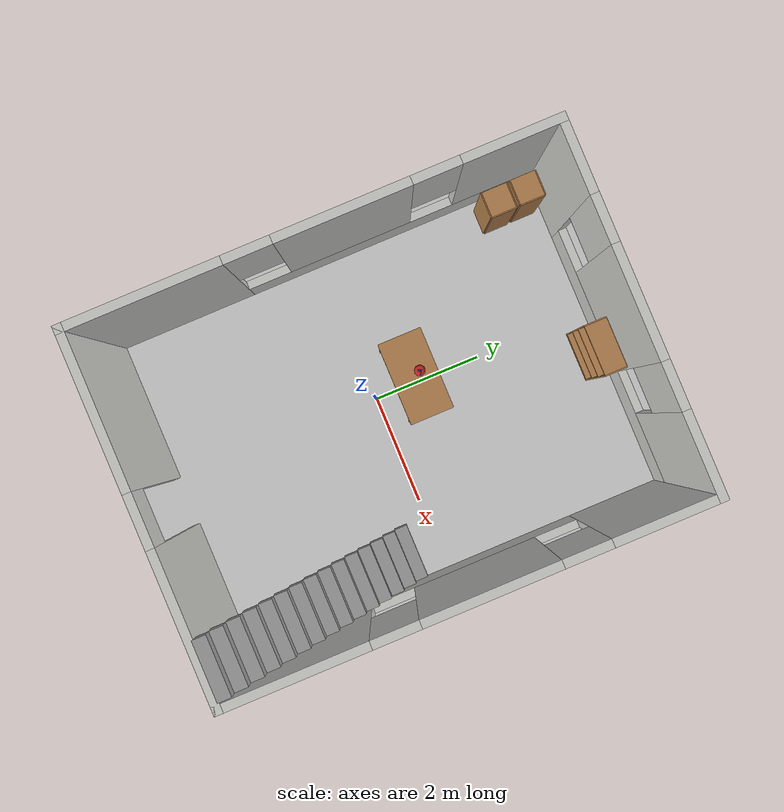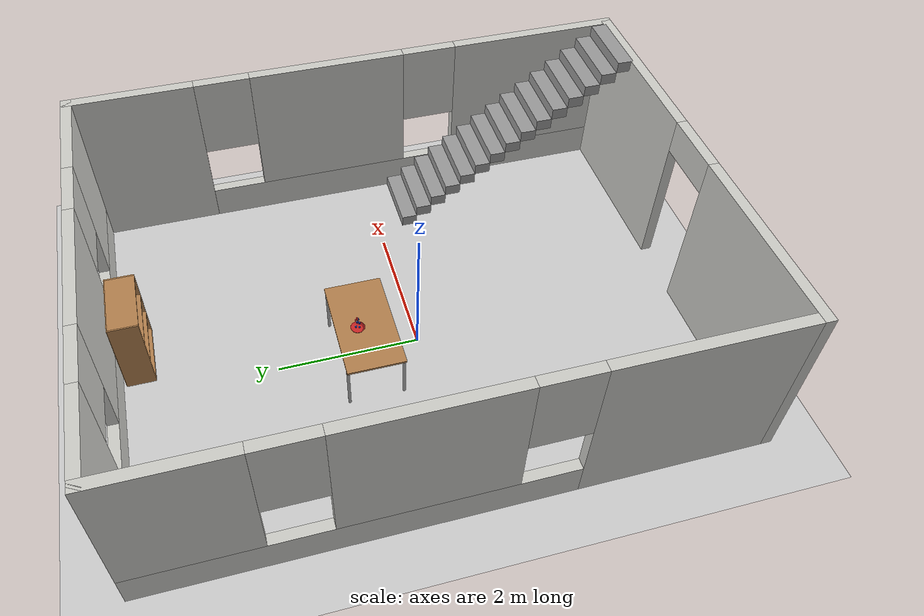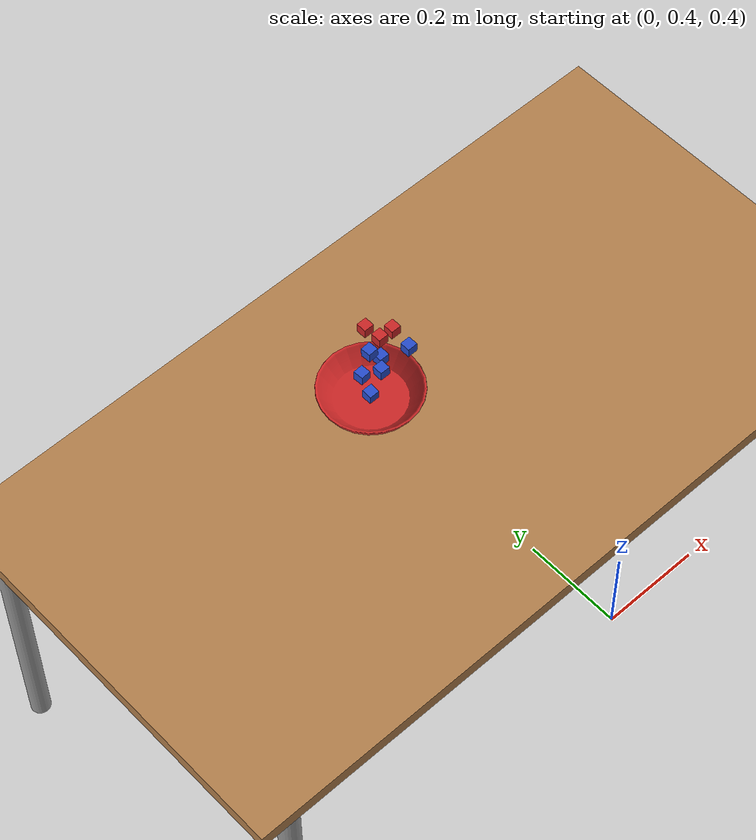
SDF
<sdf version="1.6">
 <world name="default">
  <model name="ground_plane">
   <static>1</static>
   <link name="link">
    <collision name="collision">
     <geometry><plane><normal>0 0 1</normal><size>100 100</size></plane></geometry>
     <surface><friction><ode><mu>100</mu><mu2>50</mu2></ode></friction></surface>
    </collision>
    <visual name="visual">
     <cast_shadows>0</cast_shadows>
     <geometry><plane><normal>0 0 1</normal><size>100 100</size></plane></geometry>
     <material>
      <script><uri>file://media/materials/scripts/gazebo.material</uri><name>Gazebo/Grey</name></script>
     </material>
    </visual>
   </link>
  </model>
  <model name="table">
   <static>1</static>
   <link name="table">
    <collision name="surface">
     <pose>0 0 1 0 -0 0</pose>
     <geometry><box><size>1.5 0.8 0.03</size></box></geometry>
     <surface><friction><ode><mu>0.6</mu><mu2>0.6</mu2></ode></friction></surface>
    </collision>
    <visual name="visual1">
     <pose>0 0 1 0 -0 0</pose>
     <geometry><box><size>1.5 0.8 0.03</size></box></geometry>
     <material>
      <script><uri>file://media/materials/scripts/gazebo.material</uri><name>Gazebo/Wood</name></script>
     </material>
    </visual>
    <collision name="front_left_leg">
     <pose>0.68 0.38 0.5 0 -0 0</pose>
     <geometry><cylinder><radius>0.02</radius><length>1</length></cylinder></geometry>
    </collision>
    <visual name="front_left_leg">
     <pose>0.68 0.38 0.5 0 -0 0</pose>
     <geometry><cylinder><radius>0.02</radius><length>1</length></cylinder></geometry>
     <material>
      <script><uri>file://media/materials/scripts/gazebo.material</uri><name>Gazebo/Grey</name></script>
     </material>
    </visual>
    <collision name="front_right_leg">
     <pose>0.68 -0.38 0.5 0 -0 0</pose>
     <geometry><cylinder><radius>0.02</radius><length>1</length></cylinder></geometry>
    </collision>
    <visual name="front_right_leg">
     <pose>0.68 -0.38 0.5 0 -0 0</pose>
     <geometry><cylinder><radius>0.02</radius><length>1</length></cylinder></geometry>
     <material>
      <script><uri>file://media/materials/scripts/gazebo.material</uri><name>Gazebo/Grey</name></script>
     </material>
    </visual>
    <collision name="back_right_leg">
     <pose>-0.68 -0.38 0.5 0 -0 0</pose>
     <geometry><cylinder><radius>0.02</radius><length>1</length></cylinder></geometry>
    </collision>
    <visual name="back_right_leg">
     <pose>-0.68 -0.38 0.5 0 -0 0</pose>
     <geometry><cylinder><radius>0.02</radius><length>1</length></cylinder></geometry>
     <material>
      <script><uri>file://media/materials/scripts/gazebo.material</uri><name>Gazebo/Grey</name></script>
     </material>
    </visual>
    <collision name="back_left_leg">
     <pose>-0.68 0.38 0.5 0 -0 0</pose>
     <geometry><cylinder><radius>0.02</radius><length>1</length></cylinder></geometry>
    </collision>
    <visual name="back_left_leg">
     <pose>-0.68 0.38 0.5 0 -0 0</pose>
     <geometry><cylinder><radius>0.02</radius><length>1</length></cylinder></geometry>
     <material>
      <script><uri>file://media/materials/scripts/gazebo.material</uri><name>Gazebo/Grey</name></script>
     </material>
    </visual>
   </link>
   <pose>-0.08 0.78 -0.29 0 -0 0</pose>
  </model>
  <scene><ambient>0.4 0.4 0.4 1</ambient><background>0.25 0.25 0.25 1</background><shadows>0</shadows></scene>
  <light name="light1" type="directional">
   <diffuse>1 1 1 0</diffuse>
   <specular>1 1 1 0</specular>
   <direction>-1 -1 -1</direction>
  </light>
  <light name="light2" type="directional">
   <diffuse>0 0 0 0</diffuse>
   <specular>1 1 1 0</specular>
   <direction>-1 -1 -1</direction>
  </light>
  <light name="light3" type="directional">
   <diffuse>0 0 0 0</diffuse>
   <specular>1 1 1 0</specular>
   <direction>-1 -1 -1</direction>
  </light>
  <light name="light4" type="directional">
   <diffuse>0 0 0 0</diffuse>
   <specular>1 1 1 0</specular>
   <direction>-1 -1 -1</direction>
  </light>
  <light name="light5" type="directional">
   <diffuse>0 0 0 0</diffuse>
   <specular>1 1 1 0</specular>
   <direction>-1 -1 -1</direction>
  </light>
  <light name="light6" type="directional">
   <diffuse>0 0 0 0</diffuse>
   <specular>1 1 1 0</specular>
   <direction>-1 -1 -1</direction>
  </light>
  <gravity>0 0 -9.8</gravity>
  <magnetic_field>6e-06 2.3e-05 -4.2e-05</magnetic_field>
  <atmosphere type="adiabatic"/>
  <physics name="default_physics" default="0" type="ode">
   <max_step_size>0.001</max_step_size>
   <real_time_factor>1</real_time_factor>
   <real_time_update_rate>1000</real_time_update_rate>
  </physics>
  <spherical_coordinates>
   <surface_model>EARTH_WGS84</surface_model>
   <latitude_deg>0</latitude_deg>
   <longitude_deg>0</longitude_deg>
   <elevation>0</elevation>
   <heading_deg>0</heading_deg>
  </spherical_coordinates>
  <model name="home">
   <pose>0.349793 0.122852 0 0 -0 0</pose>
   <link name="Stairs_0">
    <visual name="Stairs_0_Visual_0">
     <pose>2.45797 -0.622751 0.083333 0 -0 0</pose>
     <geometry><box><size>1 0.233333 0.166667</size></box></geometry>
     <material>
      <script><uri>file://media/materials/scripts/gazebo.material</uri><name>Gazebo/Grey</name></script>
      <ambient>1 1 1 1</ambient>
     </material>
     <meta><layer>0</layer></meta>
    </visual>
    <collision name="Stairs_0_Collision_0">
     <geometry><box><size>1 0.233333 0.166667</size></box></geometry>
     <pose>2.45797 -0.622751 0.083333 0 -0 0</pose>
    </collision>
    <visual name="Stairs_0_Visual_1">
     <pose>2.45797 -0.856085 0.25 0 -0 0</pose>
     <geometry><box><size>1 0.233333 0.166667</size></box></geometry>
     <material>
      <script><uri>file://media/materials/scripts/gazebo.material</uri><name>Gazebo/Grey</name></script>
      <ambient>1 1 1 1</ambient>
     </material>
     <meta><layer>0</layer></meta>
    </visual>
    <collision name="Stairs_0_Collision_1">
     <geometry><box><size>1 0.233333 0.166667</size></box></geometry>
     <pose>2.45797 -0.856085 0.25 0 -0 0</pose>
    </collision>
    <visual name="Stairs_0_Visual_2">
     <pose>2.45797 -1.08942 0.416667 0 -0 0</pose>
     <geometry><box><size>1 0.233333 0.166667</size></box></geometry>
     <material>
      <script><uri>file://media/materials/scripts/gazebo.material</uri><name>Gazebo/Grey</name></script>
      <ambient>1 1 1 1</ambient>
     </material>
     <meta><layer>0</layer></meta>
    </visual>
    <collision name="Stairs_0_Collision_2">
     <geometry><box><size>1 0.233333 0.166667</size></box></geometry>
     <pose>2.45797 -1.08942 0.416667 0 -0 0</pose>
    </collision>
    <visual name="Stairs_0_Visual_3">
     <pose>2.45797 -1.32275 0.583333 0 -0 0</pose>
     <geometry><box><size>1 0.233333 0.166667</size></box></geometry>
     <material>
      <script><uri>file://media/materials/scripts/gazebo.material</uri><name>Gazebo/Grey</name></script>
      <ambient>1 1 1 1</ambient>
     </material>
     <meta><layer>0</layer></meta>
    </visual>
    <collision name="Stairs_0_Collision_3">
     <geometry><box><size>1 0.233333 0.166667</size></box></geometry>
     <pose>2.45797 -1.32275 0.583333 0 -0 0</pose>
    </collision>
    <visual name="Stairs_0_Visual_4">
     <pose>2.45797 -1.55608 0.75 0 -0 0</pose>
     <geometry><box><size>1 0.233333 0.166667</size></box></geometry>
     <material>
      <script><uri>file://media/materials/scripts/gazebo.material</uri><name>Gazebo/Grey</name></script>
      <ambient>1 1 1 1</ambient>
     </material>
     <meta><layer>0</layer></meta>
    </visual>
    <collision name="Stairs_0_Collision_4">
     <geometry><box><size>1 0.233333 0.166667</size></box></geometry>
     <pose>2.45797 -1.55608 0.75 0 -0 0</pose>
    </collision>
    <visual name="Stairs_0_Visual_5">
     <pose>2.45797 -1.78942 0.916667 0 -0 0</pose>
     <geometry><box><size>1 0.233333 0.166667</size></box></geometry>
     <material>
      <script><uri>file://media/materials/scripts/gazebo.material</uri><name>Gazebo/Grey</name></script>
      <ambient>1 1 1 1</ambient>
     </material>
     <meta><layer>0</layer></meta>
    </visual>
    <collision name="Stairs_0_Collision_5">
     <geometry><box><size>1 0.233333 0.166667</size></box></geometry>
     <pose>2.45797 -1.78942 0.916667 0 -0 0</pose>
    </collision>
    <visual name="Stairs_0_Visual_6">
     <pose>2.45797 -2.02275 1.08333 0 -0 0</pose>
     <geometry><box><size>1 0.233333 0.166667</size></box></geometry>
     <material>
      <script><uri>file://media/materials/scripts/gazebo.material</uri><name>Gazebo/Grey</name></script>
      <ambient>1 1 1 1</ambient>
     </material>
     <meta><layer>0</layer></meta>
    </visual>
    <collision name="Stairs_0_Collision_6">
     <geometry><box><size>1 0.233333 0.166667</size></box></geometry>
     <pose>2.45797 -2.02275 1.08333 0 -0 0</pose>
    </collision>
    <visual name="Stairs_0_Visual_7">
     <pose>2.45797 -2.25609 1.25 0 -0 0</pose>
     <geometry><box><size>1 0.233333 0.166667</size></box></geometry>
     <material>
      <script><uri>file://media/materials/scripts/gazebo.material</uri><name>Gazebo/Grey</name></script>
      <ambient>1 1 1 1</ambient>
     </material>
     <meta><layer>0</layer></meta>
    </visual>
    <collision name="Stairs_0_Collision_7">
     <geometry><box><size>1 0.233333 0.166667</size></box></geometry>
     <pose>2.45797 -2.25609 1.25 0 -0 0</pose>
    </collision>
    <visual name="Stairs_0_Visual_8">
     <pose>2.45797 -2.48942 1.41667 0 -0 0</pose>
     <geometry><box><size>1 0.233333 0.166667</size></box></geometry>
     <material>
      <script><uri>file://media/materials/scripts/gazebo.material</uri><name>Gazebo/Grey</name></script>
      <ambient>1 1 1 1</ambient>
     </material>
     <meta><layer>0</layer></meta>
    </visual>
    <collision name="Stairs_0_Collision_8">
     <geometry><box><size>1 0.233333 0.166667</size></box></geometry>
     <pose>2.45797 -2.48942 1.41667 0 -0 0</pose>
    </collision>
    <visual name="Stairs_0_Visual_9">
     <pose>2.45797 -2.72275 1.58333 0 -0 0</pose>
     <geometry><box><size>1 0.233333 0.166667</size></box></geometry>
     <material>
      <script><uri>file://media/materials/scripts/gazebo.material</uri><name>Gazebo/Grey</name></script>
      <ambient>1 1 1 1</ambient>
     </material>
     <meta><layer>0</layer></meta>
    </visual>
    <collision name="Stairs_0_Collision_9">
     <geometry><box><size>1 0.233333 0.166667</size></box></geometry>
     <pose>2.45797 -2.72275 1.58333 0 -0 0</pose>
    </collision>
    <visual name="Stairs_0_Visual_10">
     <pose>2.45797 -2.95608 1.75 0 -0 0</pose>
     <geometry><box><size>1 0.233333 0.166667</size></box></geometry>
     <material>
      <script><uri>file://media/materials/scripts/gazebo.material</uri><name>Gazebo/Grey</name></script>
      <ambient>1 1 1 1</ambient>
     </material>
     <meta><layer>0</layer></meta>
    </visual>
    <collision name="Stairs_0_Collision_10">
     <geometry><box><size>1 0.233333 0.166667</size></box></geometry>
     <pose>2.45797 -2.95608 1.75 0 -0 0</pose>
    </collision>
    <visual name="Stairs_0_Visual_11">
     <pose>2.45797 -3.18942 1.91667 0 -0 0</pose>
     <geometry><box><size>1 0.233333 0.166667</size></box></geometry>
     <material>
      <script><uri>file://media/materials/scripts/gazebo.material</uri><name>Gazebo/Grey</name></script>
      <ambient>1 1 1 1</ambient>
     </material>
     <meta><layer>0</layer></meta>
    </visual>
    <collision name="Stairs_0_Collision_11">
     <geometry><box><size>1 0.233333 0.166667</size></box></geometry>
     <pose>2.45797 -3.18942 1.91667 0 -0 0</pose>
    </collision>
    <visual name="Stairs_0_Visual_12">
     <pose>2.45797 -3.42275 2.08333 0 -0 0</pose>
     <geometry><box><size>1 0.233333 0.166667</size></box></geometry>
     <material>
      <script><uri>file://media/materials/scripts/gazebo.material</uri><name>Gazebo/Grey</name></script>
      <ambient>1 1 1 1</ambient>
     </material>
     <meta><layer>0</layer></meta>
    </visual>
    <collision name="Stairs_0_Collision_12">
     <geometry><box><size>1 0.233333 0.166667</size></box></geometry>
     <pose>2.45797 -3.42275 2.08333 0 -0 0</pose>
    </collision>
    <visual name="Stairs_0_Visual_13">
     <pose>2.45797 -3.65609 2.25 0 -0 0</pose>
     <geometry><box><size>1 0.233333 0.166667</size></box></geometry>
     <material>
      <script><uri>file://media/materials/scripts/gazebo.material</uri><name>Gazebo/Grey</name></script>
      <ambient>1 1 1 1</ambient>
     </material>
     <meta><layer>0</layer></meta>
    </visual>
    <collision name="Stairs_0_Collision_13">
     <geometry><box><size>1 0.233333 0.166667</size></box></geometry>
     <pose>2.45797 -3.65609 2.25 0 -0 0</pose>
    </collision>
    <visual name="Stairs_0_Visual_14">
     <pose>2.45797 -3.88942 2.41667 0 -0 0</pose>
     <geometry><box><size>1 0.233333 0.166667</size></box></geometry>
     <material>
      <script><uri>file://media/materials/scripts/gazebo.material</uri><name>Gazebo/Grey</name></script>
      <ambient>1 1 1 1</ambient>
     </material>
     <meta><layer>0</layer></meta>
    </visual>
    <collision name="Stairs_0_Collision_14">
     <geometry><box><size>1 0.233333 0.166667</size></box></geometry>
     <pose>2.45797 -3.88942 2.41667 0 -0 0</pose>
    </collision>
   </link>
   <link name="Wall_0">
    <pose>0 -4.05 0 0 -0 3.14159</pose>
    <visual name="Wall_0_Visual_0">
     <pose>-1.80618 0 1.25 0 -0 0</pose>
     <geometry><box><size>2.63764 0.15 2.5</size></box></geometry>
     <material>
      <script><uri>file://media/materials/scripts/gazebo.material</uri><name>Gazebo/CeilingTiled</name></script>
      <ambient>1 1 1 1</ambient>
     </material>
     <meta><layer>0</layer></meta>
    </visual>
    <collision name="Wall_0_Collision_0">
     <geometry><box><size>2.63764 0.15 2.5</size></box></geometry>
     <pose>-1.80618 0 1.25 0 -0 0</pose>
    </collision>
    <visual name="Wall_0_Visual_1">
     <pose>1.76882 0 1.25 0 -0 0</pose>
     <geometry><box><size>2.71236 0.15 2.5</size></box></geometry>
     <material>
      <script><uri>file://media/materials/scripts/gazebo.material</uri><name>Gazebo/CeilingTiled</name></script>
      <ambient>1 1 1 1</ambient>
     </material>
     <meta><layer>0</layer></meta>
    </visual>
    <collision name="Wall_0_Collision_1">
     <geometry><box><size>2.71236 0.15 2.5</size></box></geometry>
     <pose>1.76882 0 1.25 0 -0 0</pose>
    </collision>
    <visual name="Wall_0_Visual_2">
     <pose>-0.037357 0 2.25 0 -0 0</pose>
     <geometry><box><size>0.9 0.15 0.5</size></box></geometry>
     <material>
      <script><uri>file://media/materials/scripts/gazebo.material</uri><name>Gazebo/CeilingTiled</name></script>
      <ambient>1 1 1 1</ambient>
     </material>
     <meta><layer>0</layer></meta>
    </visual>
    <collision name="Wall_0_Collision_2">
     <geometry><box><size>0.9 0.15 0.5</size></box></geometry>
     <pose>-0.037357 0 2.25 0 -0 0</pose>
    </collision>
   </link>
   <link name="Wall_1">
    <pose>-3.05 0 0 0 -0 1.5708</pose>
    <visual name="Wall_1_Visual_0">
     <pose>-2.77874 0 1.25 0 -0 0</pose>
     <geometry><box><size>2.69252 0.15 2.5</size></box></geometry>
     <material>
      <script><uri>file://media/materials/scripts/gazebo.material</uri><name>Gazebo/CeilingTiled</name></script>
      <ambient>1 1 1 1</ambient>
     </material>
     <meta><layer>0</layer></meta>
    </visual>
    <collision name="Wall_1_Collision_0">
     <geometry><box><size>2.69252 0.15 2.5</size></box></geometry>
     <pose>-2.77874 0 1.25 0 -0 0</pose>
    </collision>
    <visual name="Wall_1_Visual_1">
     <pose>1.34626 0 0.25 0 -0 0</pose>
     <geometry><box><size>5.55748 0.15 0.5</size></box></geometry>
     <material>
      <script><uri>file://media/materials/scripts/gazebo.material</uri><name>Gazebo/CeilingTiled</name></script>
      <ambient>1 1 1 1</ambient>
     </material>
     <meta><layer>0</layer></meta>
    </visual>
    <collision name="Wall_1_Collision_1">
     <geometry><box><size>5.55748 0.15 0.5</size></box></geometry>
     <pose>1.34626 0 0.25 0 -0 0</pose>
    </collision>
    <visual name="Wall_1_Visual_2">
     <pose>0.497036 0 1.5 0 -0 0</pose>
     <geometry><box><size>2.25902 0.15 2</size></box></geometry>
     <material>
      <script><uri>file://media/materials/scripts/gazebo.material</uri><name>Gazebo/CeilingTiled</name></script>
      <ambient>1 1 1 1</ambient>
     </material>
     <meta><layer>0</layer></meta>
    </visual>
    <collision name="Wall_1_Collision_2">
     <geometry><box><size>2.25902 0.15 2</size></box></geometry>
     <pose>0.497036 0 1.5 0 -0 0</pose>
    </collision>
    <visual name="Wall_1_Visual_3">
     <pose>3.27577 0 1.5 0 -0 0</pose>
     <geometry><box><size>1.69845 0.15 2</size></box></geometry>
     <material>
      <script><uri>file://media/materials/scripts/gazebo.material</uri><name>Gazebo/CeilingTiled</name></script>
      <ambient>1 1 1 1</ambient>
     </material>
     <meta><layer>0</layer></meta>
    </visual>
    <collision name="Wall_1_Collision_3">
     <geometry><box><size>1.69845 0.15 2</size></box></geometry>
     <pose>3.27577 0 1.5 0 -0 0</pose>
    </collision>
    <visual name="Wall_1_Visual_4">
     <pose>-1.03248 0 1.9 0 -0 0</pose>
     <geometry><box><size>0.8 0.15 1.2</size></box></geometry>
     <material>
      <script><uri>file://media/materials/scripts/gazebo.material</uri><name>Gazebo/CeilingTiled</name></script>
      <ambient>1 1 1 1</ambient>
     </material>
     <meta><layer>0</layer></meta>
    </visual>
    <collision name="Wall_1_Collision_4">
     <geometry><box><size>0.8 0.15 1.2</size></box></geometry>
     <pose>-1.03248 0 1.9 0 -0 0</pose>
    </collision>
    <visual name="Wall_1_Visual_5">
     <pose>2.02655 0 1.9 0 -0 0</pose>
     <geometry><box><size>0.8 0.15 1.2</size></box></geometry>
     <material>
      <script><uri>file://media/materials/scripts/gazebo.material</uri><name>Gazebo/CeilingTiled</name></script>
      <ambient>1 1 1 1</ambient>
     </material>
     <meta><layer>0</layer></meta>
    </visual>
    <collision name="Wall_1_Collision_5">
     <geometry><box><size>0.8 0.15 1.2</size></box></geometry>
     <pose>2.02655 0 1.9 0 -0 0</pose>
    </collision>
   </link>
   <link name="Wall_2">
    <pose>0 4.05 0 0 -0 0</pose>
    <visual name="Wall_2_Visual_0">
     <pose>-2.47533 0 1.25 0 -0 0</pose>
     <geometry><box><size>1.29935 0.15 2.5</size></box></geometry>
     <material>
      <script><uri>file://media/materials/scripts/gazebo.material</uri><name>Gazebo/CeilingTiled</name></script>
      <ambient>1 1 1 1</ambient>
     </material>
     <meta><layer>0</layer></meta>
    </visual>
    <collision name="Wall_2_Collision_0">
     <geometry><box><size>1.29935 0.15 2.5</size></box></geometry>
     <pose>-2.47533 0 1.25 0 -0 0</pose>
    </collision>
    <visual name="Wall_2_Visual_1">
     <pose>0.649673 0 0.25 0 -0 0</pose>
     <geometry><box><size>4.95065 0.15 0.5</size></box></geometry>
     <material>
      <script><uri>file://media/materials/scripts/gazebo.material</uri><name>Gazebo/CeilingTiled</name></script>
      <ambient>1 1 1 1</ambient>
     </material>
     <meta><layer>0</layer></meta>
    </visual>
    <collision name="Wall_2_Collision_1">
     <geometry><box><size>4.95065 0.15 0.5</size></box></geometry>
     <pose>0.649673 0 0.25 0 -0 0</pose>
    </collision>
    <visual name="Wall_2_Visual_2">
     <pose>-0.082344 0 1.5 0 -0 0</pose>
     <geometry><box><size>1.88662 0.15 2</size></box></geometry>
     <material>
      <script><uri>file://media/materials/scripts/gazebo.material</uri><name>Gazebo/CeilingTiled</name></script>
      <ambient>1 1 1 1</ambient>
     </material>
     <meta><layer>0</layer></meta>
    </visual>
    <collision name="Wall_2_Collision_2">
     <geometry><box><size>1.88662 0.15 2</size></box></geometry>
     <pose>-0.082344 0 1.5 0 -0 0</pose>
    </collision>
    <visual name="Wall_2_Visual_3">
     <pose>2.39298 0 1.5 0 -0 0</pose>
     <geometry><box><size>1.46403 0.15 2</size></box></geometry>
     <material>
      <script><uri>file://media/materials/scripts/gazebo.material</uri><name>Gazebo/CeilingTiled</name></script>
      <ambient>1 1 1 1</ambient>
     </material>
     <meta><layer>0</layer></meta>
    </visual>
    <collision name="Wall_2_Collision_3">
     <geometry><box><size>1.46403 0.15 2</size></box></geometry>
     <pose>2.39298 0 1.5 0 -0 0</pose>
    </collision>
    <visual name="Wall_2_Visual_4">
     <pose>-1.42565 0 1.9 0 -0 0</pose>
     <geometry><box><size>0.8 0.15 1.2</size></box></geometry>
     <material>
      <script><uri>file://media/materials/scripts/gazebo.material</uri><name>Gazebo/CeilingTiled</name></script>
      <ambient>1 1 1 1</ambient>
     </material>
     <meta><layer>0</layer></meta>
    </visual>
    <collision name="Wall_2_Collision_4">
     <geometry><box><size>0.8 0.15 1.2</size></box></geometry>
     <pose>-1.42565 0 1.9 0 -0 0</pose>
    </collision>
    <visual name="Wall_2_Visual_5">
     <pose>1.26097 0 1.9 0 -0 0</pose>
     <geometry><box><size>0.8 0.15 1.2</size></box></geometry>
     <material>
      <script><uri>file://media/materials/scripts/gazebo.material</uri><name>Gazebo/CeilingTiled</name></script>
      <ambient>1 1 1 1</ambient>
     </material>
     <meta><layer>0</layer></meta>
    </visual>
    <collision name="Wall_2_Collision_5">
     <geometry><box><size>0.8 0.15 1.2</size></box></geometry>
     <pose>1.26097 0 1.9 0 -0 0</pose>
    </collision>
   </link>
   <link name="Wall_3">
    <pose>3.05 0 0 0 0 -1.5708</pose>
    <visual name="Wall_3_Visual_0">
     <pose>-3.20927 0 1.25 0 -0 0</pose>
     <geometry><box><size>1.83145 0.15 2.5</size></box></geometry>
     <material>
      <script><uri>file://media/materials/scripts/gazebo.material</uri><name>Gazebo/CeilingTiled</name></script>
      <ambient>1 1 1 1</ambient>
     </material>
     <meta><layer>0</layer></meta>
    </visual>
    <collision name="Wall_3_Collision_0">
     <geometry><box><size>1.83145 0.15 2.5</size></box></geometry>
     <pose>-3.20927 0 1.25 0 -0 0</pose>
    </collision>
    <visual name="Wall_3_Visual_1">
     <pose>0.915727 0 0.25 0 -0 0</pose>
     <geometry><box><size>6.41855 0.15 0.5</size></box></geometry>
     <material>
      <script><uri>file://media/materials/scripts/gazebo.material</uri><name>Gazebo/CeilingTiled</name></script>
      <ambient>1 1 1 1</ambient>
     </material>
     <meta><layer>0</layer></meta>
    </visual>
    <collision name="Wall_3_Collision_1">
     <geometry><box><size>6.41855 0.15 0.5</size></box></geometry>
     <pose>0.915727 0 0.25 0 -0 0</pose>
    </collision>
    <visual name="Wall_3_Visual_2">
     <pose>-0.350735 0 1.5 0 -0 0</pose>
     <geometry><box><size>2.28562 0.15 2</size></box></geometry>
     <material>
      <script><uri>file://media/materials/scripts/gazebo.material</uri><name>Gazebo/CeilingTiled</name></script>
      <ambient>1 1 1 1</ambient>
     </material>
     <meta><layer>0</layer></meta>
    </visual>
    <collision name="Wall_3_Collision_2">
     <geometry><box><size>2.28562 0.15 2</size></box></geometry>
     <pose>-0.350735 0 1.5 0 -0 0</pose>
    </collision>
    <visual name="Wall_3_Visual_3">
     <pose>2.85854 0 1.5 0 -0 0</pose>
     <geometry><box><size>2.53292 0.15 2</size></box></geometry>
     <material>
      <script><uri>file://media/materials/scripts/gazebo.material</uri><name>Gazebo/CeilingTiled</name></script>
      <ambient>1 1 1 1</ambient>
     </material>
     <meta><layer>0</layer></meta>
    </visual>
    <collision name="Wall_3_Collision_3">
     <geometry><box><size>2.53292 0.15 2</size></box></geometry>
     <pose>2.85854 0 1.5 0 -0 0</pose>
    </collision>
    <visual name="Wall_3_Visual_4">
     <pose>-1.89355 0 1.9 0 -0 0</pose>
     <geometry><box><size>0.8 0.15 1.2</size></box></geometry>
     <material>
      <script><uri>file://media/materials/scripts/gazebo.material</uri><name>Gazebo/CeilingTiled</name></script>
      <ambient>1 1 1 1</ambient>
     </material>
     <meta><layer>0</layer></meta>
    </visual>
    <collision name="Wall_3_Collision_4">
     <geometry><box><size>0.8 0.15 1.2</size></box></geometry>
     <pose>-1.89355 0 1.9 0 -0 0</pose>
    </collision>
    <visual name="Wall_3_Visual_5">
     <pose>1.19208 0 1.9 0 -0 0</pose>
     <geometry><box><size>0.8 0.15 1.2</size></box></geometry>
     <material>
      <script><uri>file://media/materials/scripts/gazebo.material</uri><name>Gazebo/CeilingTiled</name></script>
      <ambient>1 1 1 1</ambient>
     </material>
     <meta><layer>0</layer></meta>
    </visual>
    <collision name="Wall_3_Collision_5">
     <geometry><box><size>0.8 0.15 1.2</size></box></geometry>
     <pose>1.19208 0 1.9 0 -0 0</pose>
    </collision>
   </link>
   <static>1</static>
  </model>
  <model name="bookshelf">
   <static>1</static>
   <link name="link">
    <inertial><mass>1</mass></inertial>
    <collision name="back">
     <pose>0 0.005 0.6 0 -0 0</pose>
     <geometry><box><size>0.9 0.01 1.2</size></box></geometry>
    </collision>
    <visual name="visual1">
     <pose>0 0.005 0.6 0 -0 0</pose>
     <geometry><box><size>0.9 0.01 1.2</size></box></geometry>
     <material>
      <script><uri>file://media/materials/scripts/gazebo.material</uri><name>Gazebo/Wood</name></script>
     </material>
    </visual>
    <collision name="left_side">
     <pose>0.45 -0.195 0.6 0 -0 0</pose>
     <geometry><box><size>0.02 0.4 1.2</size></box></geometry>
    </collision>
    <visual name="visual2">
     <pose>0.45 -0.195 0.6 0 -0 0</pose>
     <geometry><box><size>0.02 0.4 1.2</size></box></geometry>
     <material>
      <script><uri>file://media/materials/scripts/gazebo.material</uri><name>Gazebo/Wood</name></script>
     </material>
    </visual>
    <collision name="right_side">
     <pose>-0.45 -0.195 0.6 0 -0 0</pose>
     <geometry><box><size>0.02 0.4 1.2</size></box></geometry>
    </collision>
    <visual name="visual3">
     <pose>-0.45 -0.195 0.6 0 -0 0</pose>
     <geometry><box><size>0.02 0.4 1.2</size></box></geometry>
     <material>
      <script><uri>file://media/materials/scripts/gazebo.material</uri><name>Gazebo/Wood</name></script>
     </material>
    </visual>
    <collision name="bottom">
     <pose>0 -0.195 0.03 0 -0 0</pose>
     <geometry><box><size>0.88 0.4 0.06</size></box></geometry>
    </collision>
    <visual name="visual4">
     <pose>0 -0.195 0.03 0 -0 0</pose>
     <geometry><box><size>0.88 0.4 0.06</size></box></geometry>
     <material>
      <script><uri>file://media/materials/scripts/gazebo.material</uri><name>Gazebo/Wood</name></script>
     </material>
    </visual>
    <collision name="top">
     <pose>0 -0.195 1.19 0 -0 0</pose>
     <geometry><box><size>0.88 0.4 0.02</size></box></geometry>
    </collision>
    <visual name="visual5">
     <pose>0 -0.195 1.19 0 -0 0</pose>
     <geometry><box><size>0.88 0.4 0.02</size></box></geometry>
     <material>
      <script><uri>file://media/materials/scripts/gazebo.material</uri><name>Gazebo/Wood</name></script>
     </material>
    </visual>
    <collision name="low_shelf">
     <pose>0 -0.195 0.43 0 -0 0</pose>
     <geometry><box><size>0.88 0.4 0.02</size></box></geometry>
    </collision>
    <visual name="visual6">
     <pose>0 -0.195 0.43 0 -0 0</pose>
     <geometry><box><size>0.88 0.4 0.02</size></box></geometry>
     <material>
      <script><uri>file://media/materials/scripts/gazebo.material</uri><name>Gazebo/Wood</name></script>
     </material>
    </visual>
    <collision name="high_shelf">
     <pose>0 -0.195 0.8 0 -0 0</pose>
     <geometry><box><size>0.88 0.4 0.02</size></box></geometry>
    </collision>
    <visual name="visual7">
     <pose>0 -0.195 0.8 0 -0 0</pose>
     <geometry><box><size>0.88 0.4 0.02</size></box></geometry>
     <material>
      <script><uri>file://media/materials/scripts/gazebo.material</uri><name>Gazebo/Wood</name></script>
     </material>
    </visual>
   </link>
   <pose>0.708876 4.04857 0 0 -0 0</pose>
  </model>
  <model name="cabinet">
   <static>1</static>
   <link name="cabinet_bottom_plate">
    <inertial>
     <pose>0 0 -1 0 -0 0</pose>
     <inertia><ixx>2.05</ixx><ixy>0</ixy><ixz>0</ixz><iyy>2.05</iyy><iyz>0</iyz><izz>2.05</izz></inertia>
     <mass>25</mass>
    </inertial>
    <collision name="cabinet_bottom_plate_geom">
     <pose>0 0 0.01 0 -0 0</pose>
     <geometry><box><size>0.45 0.45 0.02</size></box></geometry>
    </collision>
    <visual name="cabinet_bottom_plate_geom_visual">
     <pose>0 0 0.01 0 -0 0</pose>
     <geometry><box><size>0.45 0.45 0.02</size></box></geometry>
     <material>
      <script><uri>file://media/materials/scripts/gazebo.material</uri><name>Gazebo/Wood</name></script>
     </material>
    </visual>
    <collision name="cabinet_bottom_plate_geom_cabinet_back_plate">
     <pose>0.235 0 0.51 0 -0 0</pose>
     <geometry><box><size>0.02 0.45 1.02</size></box></geometry>
    </collision>
    <visual name="cabinet_bottom_plate_geom_cabinet_back_plate_visual">
     <pose>0.235 0 0.51 0 -0 0</pose>
     <geometry><box><size>0.02 0.45 1.02</size></box></geometry>
     <material>
      <script><uri>file://media/materials/scripts/gazebo.material</uri><name>Gazebo/Wood</name></script>
     </material>
    </visual>
    <collision name="cabinet_bottom_plate_geom_cabinet_left_plate">
     <pose>0 0.235 0.51 0 -0 0</pose>
     <geometry><box><size>0.45 0.02 1.02</size></box></geometry>
    </collision>
    <visual name="cabinet_bottom_plate_geom_cabinet_left_plate_visual">
     <pose>0 0.235 0.51 0 -0 0</pose>
     <geometry><box><size>0.45 0.02 1.02</size></box></geometry>
     <material>
      <script><uri>file://media/materials/scripts/gazebo.material</uri><name>Gazebo/Wood</name></script>
     </material>
    </visual>
    <collision name="cabinet_bottom_plate_geom_cabinet_middle_plate">
     <pose>0 0 0.51 0 -0 0</pose>
     <geometry><box><size>0.45 0.45 0.02</size></box></geometry>
    </collision>
    <visual name="cabinet_bottom_plate_geom_cabinet_middle_plate_visual">
     <pose>0 0 0.51 0 -0 0</pose>
     <geometry><box><size>0.45 0.45 0.02</size></box></geometry>
     <material>
      <script><uri>file://media/materials/scripts/gazebo.material</uri><name>Gazebo/Wood</name></script>
     </material>
    </visual>
    <collision name="cabinet_bottom_plate_geom_cabinet_right_plate">
     <pose>0 -0.235 0.51 0 -0 0</pose>
     <geometry><box><size>0.45 0.02 1.02</size></box></geometry>
    </collision>
    <visual name="cabinet_bottom_plate_geom_cabinet_right_plate_visual">
     <pose>0 -0.235 0.51 0 -0 0</pose>
     <geometry><box><size>0.45 0.02 1.02</size></box></geometry>
     <material>
      <script><uri>file://media/materials/scripts/gazebo.material</uri><name>Gazebo/Wood</name></script>
     </material>
    </visual>
    <collision name="cabinet_bottom_plate_geom_cabinet_top_plate">
     <pose>0 0 1.01 0 -0 0</pose>
     <geometry><box><size>0.45 0.45 0.02</size></box></geometry>
    </collision>
    <visual name="cabinet_bottom_plate_geom_cabinet_top_plate_visual">
     <pose>0 0 1.01 0 -0 0</pose>
     <geometry><box><size>0.45 0.45 0.02</size></box></geometry>
     <material>
      <script><uri>file://media/materials/scripts/gazebo.material</uri><name>Gazebo/Wood</name></script>
     </material>
    </visual>
   </link>
   <pose>-2.2726 3.74013 0 0 -0 0</pose>
  </model>
  <model name="cabinet_0">
   <static>1</static>
   <link name="cabinet_bottom_plate">
    <inertial>
     <pose>0 0 -1 0 -0 0</pose>
     <inertia><ixx>2.05</ixx><ixy>0</ixy><ixz>0</ixz><iyy>2.05</iyy><iyz>0</iyz><izz>2.05</izz></inertia>
     <mass>25</mass>
    </inertial>
    <collision name="cabinet_bottom_plate_geom">
     <pose>0 0 0.01 0 -0 0</pose>
     <geometry><box><size>0.45 0.45 0.02</size></box></geometry>
    </collision>
    <visual name="cabinet_bottom_plate_geom_visual">
     <pose>0 0 0.01 0 -0 0</pose>
     <geometry><box><size>0.45 0.45 0.02</size></box></geometry>
     <material>
      <script><uri>file://media/materials/scripts/gazebo.material</uri><name>Gazebo/Wood</name></script>
     </material>
    </visual>
    <collision name="cabinet_bottom_plate_geom_cabinet_back_plate">
     <pose>0.235 0 0.51 0 -0 0</pose>
     <geometry><box><size>0.02 0.45 1.02</size></box></geometry>
    </collision>
    <visual name="cabinet_bottom_plate_geom_cabinet_back_plate_visual">
     <pose>0.235 0 0.51 0 -0 0</pose>
     <geometry><box><size>0.02 0.45 1.02</size></box></geometry>
     <material>
      <script><uri>file://media/materials/scripts/gazebo.material</uri><name>Gazebo/Wood</name></script>
     </material>
    </visual>
    <collision name="cabinet_bottom_plate_geom_cabinet_left_plate">
     <pose>0 0.235 0.51 0 -0 0</pose>
     <geometry><box><size>0.45 0.02 1.02</size></box></geometry>
    </collision>
    <visual name="cabinet_bottom_plate_geom_cabinet_left_plate_visual">
     <pose>0 0.235 0.51 0 -0 0</pose>
     <geometry><box><size>0.45 0.02 1.02</size></box></geometry>
     <material>
      <script><uri>file://media/materials/scripts/gazebo.material</uri><name>Gazebo/Wood</name></script>
     </material>
    </visual>
    <collision name="cabinet_bottom_plate_geom_cabinet_middle_plate">
     <pose>0 0 0.51 0 -0 0</pose>
     <geometry><box><size>0.45 0.45 0.02</size></box></geometry>
    </collision>
    <visual name="cabinet_bottom_plate_geom_cabinet_middle_plate_visual">
     <pose>0 0 0.51 0 -0 0</pose>
     <geometry><box><size>0.45 0.45 0.02</size></box></geometry>
     <material>
      <script><uri>file://media/materials/scripts/gazebo.material</uri><name>Gazebo/Wood</name></script>
     </material>
    </visual>
    <collision name="cabinet_bottom_plate_geom_cabinet_right_plate">
     <pose>0 -0.235 0.51 0 -0 0</pose>
     <geometry><box><size>0.45 0.02 1.02</size></box></geometry>
    </collision>
    <visual name="cabinet_bottom_plate_geom_cabinet_right_plate_visual">
     <pose>0 -0.235 0.51 0 -0 0</pose>
     <geometry><box><size>0.45 0.02 1.02</size></box></geometry>
     <material>
      <script><uri>file://media/materials/scripts/gazebo.material</uri><name>Gazebo/Wood</name></script>
     </material>
    </visual>
    <collision name="cabinet_bottom_plate_geom_cabinet_top_plate">
     <pose>0 0 1.01 0 -0 0</pose>
     <geometry><box><size>0.45 0.45 0.02</size></box></geometry>
    </collision>
    <visual name="cabinet_bottom_plate_geom_cabinet_top_plate_visual">
     <pose>0 0 1.01 0 -0 0</pose>
     <geometry><box><size>0.45 0.45 0.02</size></box></geometry>
     <material>
      <script><uri>file://media/materials/scripts/gazebo.material</uri><name>Gazebo/Wood</name></script>
     </material>
    </visual>
   </link>
   <pose>-2.26523 3.21379 0 0 -0 0</pose>
  </model>
  <model name="a_bowl">
   <link name="link">
    <inertial>
     <pose>0 0 0.0175 0 -0 0</pose>
     <mass>0.1</mass>
     <inertia>
      <ixx>0.000250308</ixx>
      <ixy>0</ixy>
      <ixz>0</ixz>
      <iyy>0.000250308</iyy>
      <iyz>0</iyz>
      <izz>0.0004802</izz>
     </inertia>
    </inertial>
    <collision name="collision">
     <geometry><mesh><uri>model://a_bowl/meshes/bowl.dae</uri></mesh></geometry>
    </collision>
    <visual name="visual">
     <geometry><mesh><uri>model://a_bowl/meshes/bowl.dae</uri></mesh></geometry>
     <material>
      <script><uri>file://media/materials/scripts/gazebo.material</uri><name>Gazebo/Red</name></script>
     </material>
    </visual>
   </link>
   <pose>-0.140445 0.881208 0.725 0 0 -0.000181</pose>
   <static>1</static>
  </model>
  <model name="green_box_0.02m">
   <link name="link_0">
    <inertial>
     <mass>0.01</mass>
     <inertia>
      <ixx>0.000166667</ixx>
      <ixy>0</ixy>
      <ixz>0</ixz>
      <iyy>0.000166667</iyy>
      <iyz>0</iyz>
      <izz>0.000166667</izz>
     </inertia>
    </inertial>
    <visual name="visual">
     <geometry><box><size>0.02 0.02 0.02</size></box></geometry>
     <material>
      <lighting>1</lighting>
      <script><uri>file://media/materials/scripts/gazebo.material</uri><name>Gazebo/Blue</name></script>
      <shader type="normal_map_object_space"><normal_map>__default__</normal_map></shader>
      <ambient>0 1 0 1</ambient>
      <diffuse>0.7 0.7 0.7 1</diffuse>
      <specular>0.01 0.01 0.01 1</specular>
      <emissive>0 0 0 1</emissive>
     </material>
    </visual>
    <collision name="collision">
     <geometry><box><size>0.02 0.02 0.02</size></box></geometry>
     <surface>
      <friction>
       <ode><mu>1</mu><mu2>1</mu2><fdir1>0 0 0</fdir1><slip1>0</slip1><slip2>0</slip2></ode>
       <torsional>
        <coefficient>1</coefficient>
        <patch_radius>0</patch_radius>
        <surface_radius>0</surface_radius>
        <use_patch_radius>1</use_patch_radius>
        <ode><slip>0</slip></ode>
       </torsional>
      </friction>
      <bounce><restitution_coefficient>0</restitution_coefficient><threshold>1e+06</threshold></bounce>
      <contact>
       <collide_without_contact>0</collide_without_contact>
       <collide_without_contact_bitmask>1</collide_without_contact_bitmask>
       <collide_bitmask>1</collide_bitmask>
       <ode>
        <soft_cfm>0</soft_cfm>
        <soft_erp>0.2</soft_erp>
        <kp>1e+13</kp>
        <kd>1</kd>
        <max_vel>0.01</max_vel>
        <min_depth>0</min_depth>
       </ode>
       <bullet>
        <split_impulse>1</split_impulse>
        <split_impulse_penetration_threshold>-0.01</split_impulse_penetration_threshold>
        <soft_cfm>0</soft_cfm>
        <soft_erp>0.2</soft_erp>
        <kp>1e+13</kp>
        <kd>1</kd>
       </bullet>
      </contact>
     </surface>
    </collision>
   </link>
   <static>0</static>
   <pose>-0.139057 0.905414 0.768296 -0.000352 0.019851 0.06679</pose>
  </model>
  <model name="green_box_0.02m_clone">
   <link name="link_0">
    <inertial>
     <mass>0.01</mass>
     <inertia>
      <ixx>0.000166667</ixx>
      <ixy>0</ixy>
      <ixz>0</ixz>
      <iyy>0.000166667</iyy>
      <iyz>0</iyz>
      <izz>0.000166667</izz>
     </inertia>
    </inertial>
    <visual name="visual">
     <geometry><box><size>0.02 0.02 0.02</size></box></geometry>
     <material>
      <lighting>1</lighting>
      <script><uri>file://media/materials/scripts/gazebo.material</uri><name>Gazebo/Blue</name></script>
      <shader type="normal_map_object_space"><normal_map>__default__</normal_map></shader>
      <ambient>0 1 0 1</ambient>
      <diffuse>0.7 0.7 0.7 1</diffuse>
      <specular>0.01 0.01 0.01 1</specular>
      <emissive>0 0 0 1</emissive>
     </material>
    </visual>
    <collision name="collision">
     <geometry><box><size>0.02 0.02 0.02</size></box></geometry>
     <surface>
      <friction>
       <ode><mu>1</mu><mu2>1</mu2><fdir1>0 0 0</fdir1><slip1>0</slip1><slip2>0</slip2></ode>
       <torsional>
        <coefficient>1</coefficient>
        <patch_radius>0</patch_radius>
        <surface_radius>0</surface_radius>
        <use_patch_radius>1</use_patch_radius>
        <ode><slip>0</slip></ode>
       </torsional>
      </friction>
      <bounce><restitution_coefficient>0</restitution_coefficient><threshold>1e+06</threshold></bounce>
      <contact>
       <collide_without_contact>0</collide_without_contact>
       <collide_without_contact_bitmask>1</collide_without_contact_bitmask>
       <collide_bitmask>1</collide_bitmask>
       <ode>
        <soft_cfm>0</soft_cfm>
        <soft_erp>0.2</soft_erp>
        <kp>1e+13</kp>
        <kd>1</kd>
        <max_vel>0.01</max_vel>
        <min_depth>0</min_depth>
       </ode>
       <bullet>
        <split_impulse>1</split_impulse>
        <split_impulse_penetration_threshold>-0.01</split_impulse_penetration_threshold>
        <soft_cfm>0</soft_cfm>
        <soft_erp>0.2</soft_erp>
        <kp>1e+13</kp>
        <kd>1</kd>
       </bullet>
      </contact>
     </surface>
    </collision>
   </link>
   <static>0</static>
   <pose>-0.137916 0.885836 0.855787 -0.006207 -0.017602 0.054497</pose>
  </model>
  <model name="green_box_0.02m_clone_clone">
   <link name="link_0">
    <inertial>
     <mass>0.01</mass>
     <inertia>
      <ixx>0.000166667</ixx>
      <ixy>0</ixy>
      <ixz>0</ixz>
      <iyy>0.000166667</iyy>
      <iyz>0</iyz>
      <izz>0.000166667</izz>
     </inertia>
    </inertial>
    <visual name="visual">
     <geometry><box><size>0.02 0.02 0.02</size></box></geometry>
     <material>
      <lighting>1</lighting>
      <script><uri>file://media/materials/scripts/gazebo.material</uri><name>Gazebo/Blue</name></script>
      <shader type="normal_map_object_space"><normal_map>__default__</normal_map></shader>
      <ambient>0 1 0 1</ambient>
      <diffuse>0.7 0.7 0.7 1</diffuse>
      <specular>0.01 0.01 0.01 1</specular>
      <emissive>0 0 0 1</emissive>
     </material>
    </visual>
    <collision name="collision">
     <geometry><box><size>0.02 0.02 0.02</size></box></geometry>
     <surface>
      <friction>
       <ode><mu>1</mu><mu2>1</mu2><fdir1>0 0 0</fdir1><slip1>0</slip1><slip2>0</slip2></ode>
       <torsional>
        <coefficient>1</coefficient>
        <patch_radius>0</patch_radius>
        <surface_radius>0</surface_radius>
        <use_patch_radius>1</use_patch_radius>
        <ode><slip>0</slip></ode>
       </torsional>
      </friction>
      <bounce><restitution_coefficient>0</restitution_coefficient><threshold>1e+06</threshold></bounce>
      <contact>
       <collide_without_contact>0</collide_without_contact>
       <collide_without_contact_bitmask>1</collide_without_contact_bitmask>
       <collide_bitmask>1</collide_bitmask>
       <ode>
        <soft_cfm>0</soft_cfm>
        <soft_erp>0.2</soft_erp>
        <kp>1e+13</kp>
        <kd>1</kd>
        <max_vel>0.01</max_vel>
        <min_depth>0</min_depth>
       </ode>
       <bullet>
        <split_impulse>1</split_impulse>
        <split_impulse_penetration_threshold>-0.01</split_impulse_penetration_threshold>
        <soft_cfm>0</soft_cfm>
        <soft_erp>0.2</soft_erp>
        <kp>1e+13</kp>
        <kd>1</kd>
       </bullet>
      </contact>
     </surface>
    </collision>
   </link>
   <static>0</static>
   <pose>-0.158447 0.861713 0.776605 0.06488 -0.013967 0.003919</pose>
  </model>
  <model name="red_box_0.02m">
   <link name="link_0">
    <inertial>
     <mass>0.01</mass>
     <inertia>
      <ixx>0.000166667</ixx>
      <ixy>0</ixy>
      <ixz>0</ixz>
      <iyy>0.000166667</iyy>
      <iyz>0</iyz>
      <izz>0.000166667</izz>
     </inertia>
    </inertial>
    <visual name="visual">
     <geometry><box><size>0.02 0.02 0.02</size></box></geometry>
     <material>
      <lighting>1</lighting>
      <script><uri>file://media/materials/scripts/gazebo.material</uri><name>Gazebo/Red</name></script>
      <shader type="normal_map_object_space"><normal_map>__default__</normal_map></shader>
      <ambient>1 0 0 1</ambient>
      <diffuse>0.7 0.7 0.7 1</diffuse>
      <specular>0.01 0.01 0.01 1</specular>
      <emissive>0 0 0 1</emissive>
     </material>
    </visual>
    <collision name="collision">
     <geometry><box><size>0.02 0.02 0.02</size></box></geometry>
     <surface>
      <friction>
       <ode><mu>1</mu><mu2>1</mu2><fdir1>0 0 0</fdir1><slip1>0</slip1><slip2>0</slip2></ode>
       <torsional>
        <coefficient>1</coefficient>
        <patch_radius>0</patch_radius>
        <surface_radius>0</surface_radius>
        <use_patch_radius>1</use_patch_radius>
        <ode><slip>0</slip></ode>
       </torsional>
      </friction>
      <bounce><restitution_coefficient>0</restitution_coefficient><threshold>1e+06</threshold></bounce>
      <contact>
       <collide_without_contact>0</collide_without_contact>
       <collide_without_contact_bitmask>1</collide_without_contact_bitmask>
       <collide_bitmask>1</collide_bitmask>
       <ode>
        <soft_cfm>0</soft_cfm>
        <soft_erp>0.2</soft_erp>
        <kp>1e+13</kp>
        <kd>1</kd>
        <max_vel>0.01</max_vel>
        <min_depth>0</min_depth>
       </ode>
       <bullet>
        <split_impulse>1</split_impulse>
        <split_impulse_penetration_threshold>-0.01</split_impulse_penetration_threshold>
        <soft_cfm>0</soft_cfm>
        <soft_erp>0.2</soft_erp>
        <kp>1e+13</kp>
        <kd>1</kd>
       </bullet>
      </contact>
     </surface>
    </collision>
   </link>
   <static>0</static>
   <pose>-0.120917 0.8783 0.889143 0 -0 0</pose>
  </model>
  <model name="red_box_0.02m_clone">
   <link name="link_0">
    <inertial>
     <mass>0.01</mass>
     <inertia>
      <ixx>0.000166667</ixx>
      <ixy>0</ixy>
      <ixz>0</ixz>
      <iyy>0.000166667</iyy>
      <iyz>0</iyz>
      <izz>0.000166667</izz>
     </inertia>
    </inertial>
    <visual name="visual">
     <geometry><box><size>0.02 0.02 0.02</size></box></geometry>
     <material>
      <lighting>1</lighting>
      <script><uri>file://media/materials/scripts/gazebo.material</uri><name>Gazebo/Red</name></script>
      <shader type="normal_map_object_space"><normal_map>__default__</normal_map></shader>
      <ambient>1 0 0 1</ambient>
      <diffuse>0.7 0.7 0.7 1</diffuse>
      <specular>0.01 0.01 0.01 1</specular>
      <emissive>0 0 0 1</emissive>
     </material>
    </visual>
    <collision name="collision">
     <geometry><box><size>0.02 0.02 0.02</size></box></geometry>
     <surface>
      <friction>
       <ode><mu>1</mu><mu2>1</mu2><fdir1>0 0 0</fdir1><slip1>0</slip1><slip2>0</slip2></ode>
       <torsional>
        <coefficient>1</coefficient>
        <patch_radius>0</patch_radius>
        <surface_radius>0</surface_radius>
        <use_patch_radius>1</use_patch_radius>
        <ode><slip>0</slip></ode>
       </torsional>
      </friction>
      <bounce><restitution_coefficient>0</restitution_coefficient><threshold>1e+06</threshold></bounce>
      <contact>
       <collide_without_contact>0</collide_without_contact>
       <collide_without_contact_bitmask>1</collide_without_contact_bitmask>
       <collide_bitmask>1</collide_bitmask>
       <ode>
        <soft_cfm>0</soft_cfm>
        <soft_erp>0.2</soft_erp>
        <kp>1e+13</kp>
        <kd>1</kd>
        <max_vel>0.01</max_vel>
        <min_depth>0</min_depth>
       </ode>
       <bullet>
        <split_impulse>1</split_impulse>
        <split_impulse_penetration_threshold>-0.01</split_impulse_penetration_threshold>
        <soft_cfm>0</soft_cfm>
        <soft_erp>0.2</soft_erp>
        <kp>1e+13</kp>
        <kd>1</kd>
       </bullet>
      </contact>
     </surface>
    </collision>
   </link>
   <static>0</static>
   <pose>-0.09307 0.877101 0.889143 0 -0 0</pose>
  </model>
  <model name="red_box_0.02m_clone_0">
   <link name="link_0">
    <inertial>
     <mass>0.01</mass>
     <inertia>
      <ixx>0.000166667</ixx>
      <ixy>0</ixy>
      <ixz>0</ixz>
      <iyy>0.000166667</iyy>
      <iyz>0</iyz>
      <izz>0.000166667</izz>
     </inertia>
    </inertial>
    <visual name="visual">
     <geometry><box><size>0.02 0.02 0.02</size></box></geometry>
     <material>
      <lighting>1</lighting>
      <script><uri>file://media/materials/scripts/gazebo.material</uri><name>Gazebo/Red</name></script>
      <shader type="normal_map_object_space"><normal_map>__default__</normal_map></shader>
      <ambient>1 0 0 1</ambient>
      <diffuse>0.7 0.7 0.7 1</diffuse>
      <specular>0.01 0.01 0.01 1</specular>
      <emissive>0 0 0 1</emissive>
     </material>
    </visual>
    <collision name="collision">
     <geometry><box><size>0.02 0.02 0.02</size></box></geometry>
     <surface>
      <friction>
       <ode><mu>1</mu><mu2>1</mu2><fdir1>0 0 0</fdir1><slip1>0</slip1><slip2>0</slip2></ode>
       <torsional>
        <coefficient>1</coefficient>
        <patch_radius>0</patch_radius>
        <surface_radius>0</surface_radius>
        <use_patch_radius>1</use_patch_radius>
        <ode><slip>0</slip></ode>
       </torsional>
      </friction>
      <bounce><restitution_coefficient>0</restitution_coefficient><threshold>1e+06</threshold></bounce>
      <contact>
       <collide_without_contact>0</collide_without_contact>
       <collide_without_contact_bitmask>1</collide_without_contact_bitmask>
       <collide_bitmask>1</collide_bitmask>
       <ode>
        <soft_cfm>0</soft_cfm>
        <soft_erp>0.2</soft_erp>
        <kp>1e+13</kp>
        <kd>1</kd>
        <max_vel>0.01</max_vel>
        <min_depth>0</min_depth>
       </ode>
       <bullet>
        <split_impulse>1</split_impulse>
        <split_impulse_penetration_threshold>-0.01</split_impulse_penetration_threshold>
        <soft_cfm>0</soft_cfm>
        <soft_erp>0.2</soft_erp>
        <kp>1e+13</kp>
        <kd>1</kd>
       </bullet>
      </contact>
     </surface>
    </collision>
   </link>
   <static>0</static>
   <pose>-0.129594 0.904755 0.898638 0 -0 0</pose>
  </model>
  <model name="blue_box_0.02m">
   <link name="link_0">
    <inertial>
     <mass>0.01</mass>
     <inertia>
      <ixx>0.000166667</ixx>
      <ixy>0</ixy>
      <ixz>0</ixz>
      <iyy>0.000166667</iyy>
      <iyz>0</iyz>
      <izz>0.000166667</izz>
     </inertia>
    </inertial>
    <visual name="visual">
     <geometry><box><size>0.02 0.02 0.02</size></box></geometry>
     <material>
      <lighting>1</lighting>
      <script><uri>file://media/materials/scripts/gazebo.material</uri><name>Gazebo/Blue</name></script>
      <shader type="normal_map_object_space"><normal_map>__default__</normal_map></shader>
      <ambient>0 0 1 1</ambient>
      <diffuse>0.7 0.7 0.7 1</diffuse>
      <specular>0.01 0.01 0.01 1</specular>
      <emissive>0 0 0 1</emissive>
     </material>
    </visual>
    <collision name="collision">
     <geometry><box><size>0.02 0.02 0.02</size></box></geometry>
     <surface>
      <friction>
       <ode><mu>1</mu><mu2>1</mu2><fdir1>0 0 0</fdir1><slip1>0</slip1><slip2>0</slip2></ode>
       <torsional>
        <coefficient>1</coefficient>
        <patch_radius>0</patch_radius>
        <surface_radius>0</surface_radius>
        <use_patch_radius>1</use_patch_radius>
        <ode><slip>0</slip></ode>
       </torsional>
      </friction>
      <bounce><restitution_coefficient>0</restitution_coefficient><threshold>1e+06</threshold></bounce>
      <contact>
       <collide_without_contact>0</collide_without_contact>
       <collide_without_contact_bitmask>1</collide_without_contact_bitmask>
       <collide_bitmask>1</collide_bitmask>
       <ode>
        <soft_cfm>0</soft_cfm>
        <soft_erp>0.2</soft_erp>
        <kp>1e+13</kp>
        <kd>1</kd>
        <max_vel>0.01</max_vel>
        <min_depth>0</min_depth>
       </ode>
       <bullet>
        <split_impulse>1</split_impulse>
        <split_impulse_penetration_threshold>-0.01</split_impulse_penetration_threshold>
        <soft_cfm>0</soft_cfm>
        <soft_erp>0.2</soft_erp>
        <kp>1e+13</kp>
        <kd>1</kd>
       </bullet>
      </contact>
     </surface>
    </collision>
   </link>
   <static>0</static>
   <pose>-0.122026 0.874988 0.836823 0 -0 0</pose>
  </model>
  <model name="blue_box_0.02m_clone">
   <link name="link_0">
    <inertial>
     <mass>0.01</mass>
     <inertia>
      <ixx>0.000166667</ixx>
      <ixy>0</ixy>
      <ixz>0</ixz>
      <iyy>0.000166667</iyy>
      <iyz>0</iyz>
      <izz>0.000166667</izz>
     </inertia>
    </inertial>
    <visual name="visual">
     <geometry><box><size>0.02 0.02 0.02</size></box></geometry>
     <material>
      <lighting>1</lighting>
      <script><uri>file://media/materials/scripts/gazebo.material</uri><name>Gazebo/Blue</name></script>
      <shader type="normal_map_object_space"><normal_map>__default__</normal_map></shader>
      <ambient>0 0 1 1</ambient>
      <diffuse>0.7 0.7 0.7 1</diffuse>
      <specular>0.01 0.01 0.01 1</specular>
      <emissive>0 0 0 1</emissive>
     </material>
    </visual>
    <collision name="collision">
     <geometry><box><size>0.02 0.02 0.02</size></box></geometry>
     <surface>
      <friction>
       <ode><mu>1</mu><mu2>1</mu2><fdir1>0 0 0</fdir1><slip1>0</slip1><slip2>0</slip2></ode>
       <torsional>
        <coefficient>1</coefficient>
        <patch_radius>0</patch_radius>
        <surface_radius>0</surface_radius>
        <use_patch_radius>1</use_patch_radius>
        <ode><slip>0</slip></ode>
       </torsional>
      </friction>
      <bounce><restitution_coefficient>0</restitution_coefficient><threshold>1e+06</threshold></bounce>
      <contact>
       <collide_without_contact>0</collide_without_contact>
       <collide_without_contact_bitmask>1</collide_without_contact_bitmask>
       <collide_bitmask>1</collide_bitmask>
       <ode>
        <soft_cfm>0</soft_cfm>
        <soft_erp>0.2</soft_erp>
        <kp>1e+13</kp>
        <kd>1</kd>
        <max_vel>0.01</max_vel>
        <min_depth>0</min_depth>
       </ode>
       <bullet>
        <split_impulse>1</split_impulse>
        <split_impulse_penetration_threshold>-0.01</split_impulse_penetration_threshold>
        <soft_cfm>0</soft_cfm>
        <soft_erp>0.2</soft_erp>
        <kp>1e+13</kp>
        <kd>1</kd>
       </bullet>
      </contact>
     </surface>
    </collision>
   </link>
   <static>0</static>
   <pose>-0.072164 0.858395 0.836823 0 -0 0</pose>
  </model>
  <model name="blue_box_0.02m_clone_0">
   <link name="link_0">
    <inertial>
     <mass>0.01</mass>
     <inertia>
      <ixx>0.000166667</ixx>
      <ixy>0</ixy>
      <ixz>0</ixz>
      <iyy>0.000166667</iyy>
      <iyz>0</iyz>
      <izz>0.000166667</izz>
     </inertia>
    </inertial>
    <visual name="visual">
     <geometry><box><size>0.02 0.02 0.02</size></box></geometry>
     <material>
      <lighting>1</lighting>
      <script><uri>file://media/materials/scripts/gazebo.material</uri><name>Gazebo/Blue</name></script>
      <shader type="normal_map_object_space"><normal_map>__default__</normal_map></shader>
      <ambient>0 0 1 1</ambient>
      <diffuse>0.7 0.7 0.7 1</diffuse>
      <specular>0.01 0.01 0.01 1</specular>
      <emissive>0 0 0 1</emissive>
     </material>
    </visual>
    <collision name="collision">
     <geometry><box><size>0.02 0.02 0.02</size></box></geometry>
     <surface>
      <friction>
       <ode><mu>1</mu><mu2>1</mu2><fdir1>0 0 0</fdir1><slip1>0</slip1><slip2>0</slip2></ode>
       <torsional>
        <coefficient>1</coefficient>
        <patch_radius>0</patch_radius>
        <surface_radius>0</surface_radius>
        <use_patch_radius>1</use_patch_radius>
        <ode><slip>0</slip></ode>
       </torsional>
      </friction>
      <bounce><restitution_coefficient>0</restitution_coefficient><threshold>1e+06</threshold></bounce>
      <contact>
       <collide_without_contact>0</collide_without_contact>
       <collide_without_contact_bitmask>1</collide_without_contact_bitmask>
       <collide_bitmask>1</collide_bitmask>
       <ode>
        <soft_cfm>0</soft_cfm>
        <soft_erp>0.2</soft_erp>
        <kp>1e+13</kp>
        <kd>1</kd>
        <max_vel>0.01</max_vel>
        <min_depth>0</min_depth>
       </ode>
       <bullet>
        <split_impulse>1</split_impulse>
        <split_impulse_penetration_threshold>-0.01</split_impulse_penetration_threshold>
        <soft_cfm>0</soft_cfm>
        <soft_erp>0.2</soft_erp>
        <kp>1e+13</kp>
        <kd>1</kd>
       </bullet>
      </contact>
     </surface>
    </collision>
   </link>
   <static>0</static>
   <pose>-0.13959 0.85412 0.836823 0 -0 0</pose>
  </model>
  <model name="green_box_0.02m1">
   <link name="link_0">
    <inertial>
     <mass>0.01</mass>
     <inertia>
      <ixx>0.000166667</ixx>
      <ixy>0</ixy>
      <ixz>0</ixz>
      <iyy>0.000166667</iyy>
      <iyz>0</iyz>
      <izz>0.000166667</izz>
     </inertia>
    </inertial>
    <visual name="visual">
     <geometry><box><size>0.02 0.02 0.02</size></box></geometry>
     <material>
      <lighting>1</lighting>
      <script><uri>file://media/materials/scripts/gazebo.material</uri><name>Gazebo/Blue</name></script>
      <shader type="normal_map_object_space"><normal_map>__default__</normal_map></shader>
      <ambient>0 1 0 1</ambient>
      <diffuse>0.7 0.7 0.7 1</diffuse>
      <specular>0.01 0.01 0.01 1</specular>
      <emissive>0 0 0 1</emissive>
     </material>
    </visual>
    <collision name="collision">
     <geometry><box><size>0.02 0.02 0.02</size></box></geometry>
     <surface>
      <friction>
       <ode><mu>1</mu><mu2>1</mu2><fdir1>0 0 0</fdir1><slip1>0</slip1><slip2>0</slip2></ode>
       <torsional>
        <coefficient>1</coefficient>
        <patch_radius>0</patch_radius>
        <surface_radius>0</surface_radius>
        <use_patch_radius>1</use_patch_radius>
        <ode><slip>0</slip></ode>
       </torsional>
      </friction>
      <bounce><restitution_coefficient>0</restitution_coefficient><threshold>1e+06</threshold></bounce>
      <contact>
       <collide_without_contact>0</collide_without_contact>
       <collide_without_contact_bitmask>1</collide_without_contact_bitmask>
       <collide_bitmask>1</collide_bitmask>
       <ode>
        <soft_cfm>0</soft_cfm>
        <soft_erp>0.2</soft_erp>
        <kp>1e+13</kp>
        <kd>1</kd>
        <max_vel>0.01</max_vel>
        <min_depth>0</min_depth>
       </ode>
       <bullet>
        <split_impulse>1</split_impulse>
        <split_impulse_penetration_threshold>-0.01</split_impulse_penetration_threshold>
        <soft_cfm>0</soft_cfm>
        <soft_erp>0.2</soft_erp>
        <kp>1e+13</kp>
        <kd>1</kd>
       </bullet>
      </contact>
     </surface>
    </collision>
   </link>
   <static>0</static>
   <pose>-0.139057 0.905414 0.768296 -0.000352 0.019851 0.06679</pose>
  </model>
  <model name="green_box_0.02m_clone1">
   <link name="link_0">
    <inertial>
     <mass>0.01</mass>
     <inertia>
      <ixx>0.000166667</ixx>
      <ixy>0</ixy>
      <ixz>0</ixz>
      <iyy>0.000166667</iyy>
      <iyz>0</iyz>
      <izz>0.000166667</izz>
     </inertia>
    </inertial>
    <visual name="visual">
     <geometry><box><size>0.02 0.02 0.02</size></box></geometry>
     <material>
      <lighting>1</lighting>
      <script><uri>file://media/materials/scripts/gazebo.material</uri><name>Gazebo/Blue</name></script>
      <shader type="normal_map_object_space"><normal_map>__default__</normal_map></shader>
      <ambient>0 1 0 1</ambient>
      <diffuse>0.7 0.7 0.7 1</diffuse>
      <specular>0.01 0.01 0.01 1</specular>
      <emissive>0 0 0 1</emissive>
     </material>
    </visual>
    <collision name="collision">
     <geometry><box><size>0.02 0.02 0.02</size></box></geometry>
     <surface>
      <friction>
       <ode><mu>1</mu><mu2>1</mu2><fdir1>0 0 0</fdir1><slip1>0</slip1><slip2>0</slip2></ode>
       <torsional>
        <coefficient>1</coefficient>
        <patch_radius>0</patch_radius>
        <surface_radius>0</surface_radius>
        <use_patch_radius>1</use_patch_radius>
        <ode><slip>0</slip></ode>
       </torsional>
      </friction>
      <bounce><restitution_coefficient>0</restitution_coefficient><threshold>1e+06</threshold></bounce>
      <contact>
       <collide_without_contact>0</collide_without_contact>
       <collide_without_contact_bitmask>1</collide_without_contact_bitmask>
       <collide_bitmask>1</collide_bitmask>
       <ode>
        <soft_cfm>0</soft_cfm>
        <soft_erp>0.2</soft_erp>
        <kp>1e+13</kp>
        <kd>1</kd>
        <max_vel>0.01</max_vel>
        <min_depth>0</min_depth>
       </ode>
       <bullet>
        <split_impulse>1</split_impulse>
        <split_impulse_penetration_threshold>-0.01</split_impulse_penetration_threshold>
        <soft_cfm>0</soft_cfm>
        <soft_erp>0.2</soft_erp>
        <kp>1e+13</kp>
        <kd>1</kd>
       </bullet>
      </contact>
     </surface>
    </collision>
   </link>
   <static>0</static>
   <pose>-0.137916 0.885836 0.855787 -0.006207 -0.017602 0.054497</pose>
  </model>
  <model name="green_box_0.02m_clone_clone1">
   <link name="link_0">
    <inertial>
     <mass>0.01</mass>
     <inertia>
      <ixx>0.000166667</ixx>
      <ixy>0</ixy>
      <ixz>0</ixz>
      <iyy>0.000166667</iyy>
      <iyz>0</iyz>
      <izz>0.000166667</izz>
     </inertia>
    </inertial>
    <visual name="visual">
     <geometry><box><size>0.02 0.02 0.02</size></box></geometry>
     <material>
      <lighting>1</lighting>
      <script><uri>file://media/materials/scripts/gazebo.material</uri><name>Gazebo/Blue</name></script>
      <shader type="normal_map_object_space"><normal_map>__default__</normal_map></shader>
      <ambient>0 1 0 1</ambient>
      <diffuse>0.7 0.7 0.7 1</diffuse>
      <specular>0.01 0.01 0.01 1</specular>
      <emissive>0 0 0 1</emissive>
     </material>
    </visual>
    <collision name="collision">
     <geometry><box><size>0.02 0.02 0.02</size></box></geometry>
     <surface>
      <friction>
       <ode><mu>1</mu><mu2>1</mu2><fdir1>0 0 0</fdir1><slip1>0</slip1><slip2>0</slip2></ode>
       <torsional>
        <coefficient>1</coefficient>
        <patch_radius>0</patch_radius>
        <surface_radius>0</surface_radius>
        <use_patch_radius>1</use_patch_radius>
        <ode><slip>0</slip></ode>
       </torsional>
      </friction>
      <bounce><restitution_coefficient>0</restitution_coefficient><threshold>1e+06</threshold></bounce>
      <contact>
       <collide_without_contact>0</collide_without_contact>
       <collide_without_contact_bitmask>1</collide_without_contact_bitmask>
       <collide_bitmask>1</collide_bitmask>
       <ode>
        <soft_cfm>0</soft_cfm>
        <soft_erp>0.2</soft_erp>
        <kp>1e+13</kp>
        <kd>1</kd>
        <max_vel>0.01</max_vel>
        <min_depth>0</min_depth>
       </ode>
       <bullet>
        <split_impulse>1</split_impulse>
        <split_impulse_penetration_threshold>-0.01</split_impulse_penetration_threshold>
        <soft_cfm>0</soft_cfm>
        <soft_erp>0.2</soft_erp>
        <kp>1e+13</kp>
        <kd>1</kd>
       </bullet>
      </contact>
     </surface>
    </collision>
   </link>
   <static>0</static>
   <pose>-0.158447 0.861713 0.776605 0.06488 -0.013967 0.003919</pose>
  </model>
  <model name="red_box_0.02m1">
   <link name="link_0">
    <inertial>
     <mass>0.01</mass>
     <inertia>
      <ixx>0.000166667</ixx>
      <ixy>0</ixy>
      <ixz>0</ixz>
      <iyy>0.000166667</iyy>
      <iyz>0</iyz>
      <izz>0.000166667</izz>
     </inertia>
    </inertial>
    <visual name="visual">
     <geometry><box><size>0.02 0.02 0.02</size></box></geometry>
     <material>
      <lighting>1</lighting>
      <script><uri>file://media/materials/scripts/gazebo.material</uri><name>Gazebo/Red</name></script>
      <shader type="normal_map_object_space"><normal_map>__default__</normal_map></shader>
      <ambient>1 0 0 1</ambient>
      <diffuse>0.7 0.7 0.7 1</diffuse>
      <specular>0.01 0.01 0.01 1</specular>
      <emissive>0 0 0 1</emissive>
     </material>
    </visual>
    <collision name="collision">
     <geometry><box><size>0.02 0.02 0.02</size></box></geometry>
     <surface>
      <friction>
       <ode><mu>1</mu><mu2>1</mu2><fdir1>0 0 0</fdir1><slip1>0</slip1><slip2>0</slip2></ode>
       <torsional>
        <coefficient>1</coefficient>
        <patch_radius>0</patch_radius>
        <surface_radius>0</surface_radius>
        <use_patch_radius>1</use_patch_radius>
        <ode><slip>0</slip></ode>
       </torsional>
      </friction>
      <bounce><restitution_coefficient>0</restitution_coefficient><threshold>1e+06</threshold></bounce>
      <contact>
       <collide_without_contact>0</collide_without_contact>
       <collide_without_contact_bitmask>1</collide_without_contact_bitmask>
       <collide_bitmask>1</collide_bitmask>
       <ode>
        <soft_cfm>0</soft_cfm>
        <soft_erp>0.2</soft_erp>
        <kp>1e+13</kp>
        <kd>1</kd>
        <max_vel>0.01</max_vel>
        <min_depth>0</min_depth>
       </ode>
       <bullet>
        <split_impulse>1</split_impulse>
        <split_impulse_penetration_threshold>-0.01</split_impulse_penetration_threshold>
        <soft_cfm>0</soft_cfm>
        <soft_erp>0.2</soft_erp>
        <kp>1e+13</kp>
        <kd>1</kd>
       </bullet>
      </contact>
     </surface>
    </collision>
   </link>
   <static>0</static>
   <pose>-0.120917 0.8783 0.889143 0 -0 0</pose>
  </model>
  <model name="red_box_0.02m_clone1">
   <link name="link_0">
    <inertial>
     <mass>0.01</mass>
     <inertia>
      <ixx>0.000166667</ixx>
      <ixy>0</ixy>
      <ixz>0</ixz>
      <iyy>0.000166667</iyy>
      <iyz>0</iyz>
      <izz>0.000166667</izz>
     </inertia>
    </inertial>
    <visual name="visual">
     <geometry><box><size>0.02 0.02 0.02</size></box></geometry>
     <material>
      <lighting>1</lighting>
      <script><uri>file://media/materials/scripts/gazebo.material</uri><name>Gazebo/Red</name></script>
      <shader type="normal_map_object_space"><normal_map>__default__</normal_map></shader>
      <ambient>1 0 0 1</ambient>
      <diffuse>0.7 0.7 0.7 1</diffuse>
      <specular>0.01 0.01 0.01 1</specular>
      <emissive>0 0 0 1</emissive>
     </material>
    </visual>
    <collision name="collision">
     <geometry><box><size>0.02 0.02 0.02</size></box></geometry>
     <surface>
      <friction>
       <ode><mu>1</mu><mu2>1</mu2><fdir1>0 0 0</fdir1><slip1>0</slip1><slip2>0</slip2></ode>
       <torsional>
        <coefficient>1</coefficient>
        <patch_radius>0</patch_radius>
        <surface_radius>0</surface_radius>
        <use_patch_radius>1</use_patch_radius>
        <ode><slip>0</slip></ode>
       </torsional>
      </friction>
      <bounce><restitution_coefficient>0</restitution_coefficient><threshold>1e+06</threshold></bounce>
      <contact>
       <collide_without_contact>0</collide_without_contact>
       <collide_without_contact_bitmask>1</collide_without_contact_bitmask>
       <collide_bitmask>1</collide_bitmask>
       <ode>
        <soft_cfm>0</soft_cfm>
        <soft_erp>0.2</soft_erp>
        <kp>1e+13</kp>
        <kd>1</kd>
        <max_vel>0.01</max_vel>
        <min_depth>0</min_depth>
       </ode>
       <bullet>
        <split_impulse>1</split_impulse>
        <split_impulse_penetration_threshold>-0.01</split_impulse_penetration_threshold>
        <soft_cfm>0</soft_cfm>
        <soft_erp>0.2</soft_erp>
        <kp>1e+13</kp>
        <kd>1</kd>
       </bullet>
      </contact>
     </surface>
    </collision>
   </link>
   <static>0</static>
   <pose>-0.09307 0.877101 0.889143 0 -0 0</pose>
  </model>
  <model name="red_box_0.02m_clone_01">
   <link name="link_0">
    <inertial>
     <mass>0.01</mass>
     <inertia>
      <ixx>0.000166667</ixx>
      <ixy>0</ixy>
      <ixz>0</ixz>
      <iyy>0.000166667</iyy>
      <iyz>0</iyz>
      <izz>0.000166667</izz>
     </inertia>
    </inertial>
    <visual name="visual">
     <geometry><box><size>0.02 0.02 0.02</size></box></geometry>
     <material>
      <lighting>1</lighting>
      <script><uri>file://media/materials/scripts/gazebo.material</uri><name>Gazebo/Red</name></script>
      <shader type="normal_map_object_space"><normal_map>__default__</normal_map></shader>
      <ambient>1 0 0 1</ambient>
      <diffuse>0.7 0.7 0.7 1</diffuse>
      <specular>0.01 0.01 0.01 1</specular>
      <emissive>0 0 0 1</emissive>
     </material>
    </visual>
    <collision name="collision">
     <geometry><box><size>0.02 0.02 0.02</size></box></geometry>
     <surface>
      <friction>
       <ode><mu>1</mu><mu2>1</mu2><fdir1>0 0 0</fdir1><slip1>0</slip1><slip2>0</slip2></ode>
       <torsional>
        <coefficient>1</coefficient>
        <patch_radius>0</patch_radius>
        <surface_radius>0</surface_radius>
        <use_patch_radius>1</use_patch_radius>
        <ode><slip>0</slip></ode>
       </torsional>
      </friction>
      <bounce><restitution_coefficient>0</restitution_coefficient><threshold>1e+06</threshold></bounce>
      <contact>
       <collide_without_contact>0</collide_without_contact>
       <collide_without_contact_bitmask>1</collide_without_contact_bitmask>
       <collide_bitmask>1</collide_bitmask>
       <ode>
        <soft_cfm>0</soft_cfm>
        <soft_erp>0.2</soft_erp>
        <kp>1e+13</kp>
        <kd>1</kd>
        <max_vel>0.01</max_vel>
        <min_depth>0</min_depth>
       </ode>
       <bullet>
        <split_impulse>1</split_impulse>
        <split_impulse_penetration_threshold>-0.01</split_impulse_penetration_threshold>
        <soft_cfm>0</soft_cfm>
        <soft_erp>0.2</soft_erp>
        <kp>1e+13</kp>
        <kd>1</kd>
       </bullet>
      </contact>
     </surface>
    </collision>
   </link>
   <static>0</static>
   <pose>-0.129594 0.904755 0.898638 0 -0 0</pose>
  </model>
  <model name="blue_box_0.02m1">
   <link name="link_0">
    <inertial>
     <mass>0.01</mass>
     <inertia>
      <ixx>0.000166667</ixx>
      <ixy>0</ixy>
      <ixz>0</ixz>
      <iyy>0.000166667</iyy>
      <iyz>0</iyz>
      <izz>0.000166667</izz>
     </inertia>
    </inertial>
    <visual name="visual">
     <geometry><box><size>0.02 0.02 0.02</size></box></geometry>
     <material>
      <lighting>1</lighting>
      <script><uri>file://media/materials/scripts/gazebo.material</uri><name>Gazebo/Blue</name></script>
      <shader type="normal_map_object_space"><normal_map>__default__</normal_map></shader>
      <ambient>0 0 1 1</ambient>
      <diffuse>0.7 0.7 0.7 1</diffuse>
      <specular>0.01 0.01 0.01 1</specular>
      <emissive>0 0 0 1</emissive>
     </material>
    </visual>
    <collision name="collision">
     <geometry><box><size>0.02 0.02 0.02</size></box></geometry>
     <surface>
      <friction>
       <ode><mu>1</mu><mu2>1</mu2><fdir1>0 0 0</fdir1><slip1>0</slip1><slip2>0</slip2></ode>
       <torsional>
        <coefficient>1</coefficient>
        <patch_radius>0</patch_radius>
        <surface_radius>0</surface_radius>
        <use_patch_radius>1</use_patch_radius>
        <ode><slip>0</slip></ode>
       </torsional>
      </friction>
      <bounce><restitution_coefficient>0</restitution_coefficient><threshold>1e+06</threshold></bounce>
      <contact>
       <collide_without_contact>0</collide_without_contact>
       <collide_without_contact_bitmask>1</collide_without_contact_bitmask>
       <collide_bitmask>1</collide_bitmask>
       <ode>
        <soft_cfm>0</soft_cfm>
        <soft_erp>0.2</soft_erp>
        <kp>1e+13</kp>
        <kd>1</kd>
        <max_vel>0.01</max_vel>
        <min_depth>0</min_depth>
       </ode>
       <bullet>
        <split_impulse>1</split_impulse>
        <split_impulse_penetration_threshold>-0.01</split_impulse_penetration_threshold>
        <soft_cfm>0</soft_cfm>
        <soft_erp>0.2</soft_erp>
        <kp>1e+13</kp>
        <kd>1</kd>
       </bullet>
      </contact>
     </surface>
    </collision>
   </link>
   <static>0</static>
   <pose>-0.122026 0.874988 0.836823 0 -0 0</pose>
  </model>
  <model name="blue_box_0.02m_clone1">
   <link name="link_0">
    <inertial>
     <mass>0.01</mass>
     <inertia>
      <ixx>0.000166667</ixx>
      <ixy>0</ixy>
      <ixz>0</ixz>
      <iyy>0.000166667</iyy>
      <iyz>0</iyz>
      <izz>0.000166667</izz>
     </inertia>
    </inertial>
    <visual name="visual">
     <geometry><box><size>0.02 0.02 0.02</size></box></geometry>
     <material>
      <lighting>1</lighting>
      <script><uri>file://media/materials/scripts/gazebo.material</uri><name>Gazebo/Blue</name></script>
      <shader type="normal_map_object_space"><normal_map>__default__</normal_map></shader>
      <ambient>0 0 1 1</ambient>
      <diffuse>0.7 0.7 0.7 1</diffuse>
      <specular>0.01 0.01 0.01 1</specular>
      <emissive>0 0 0 1</emissive>
     </material>
    </visual>
    <collision name="collision">
     <geometry><box><size>0.02 0.02 0.02</size></box></geometry>
     <surface>
      <friction>
       <ode><mu>1</mu><mu2>1</mu2><fdir1>0 0 0</fdir1><slip1>0</slip1><slip2>0</slip2></ode>
       <torsional>
        <coefficient>1</coefficient>
        <patch_radius>0</patch_radius>
        <surface_radius>0</surface_radius>
        <use_patch_radius>1</use_patch_radius>
        <ode><slip>0</slip></ode>
       </torsional>
      </friction>
      <bounce><restitution_coefficient>0</restitution_coefficient><threshold>1e+06</threshold></bounce>
      <contact>
       <collide_without_contact>0</collide_without_contact>
       <collide_without_contact_bitmask>1</collide_without_contact_bitmask>
       <collide_bitmask>1</collide_bitmask>
       <ode>
        <soft_cfm>0</soft_cfm>
        <soft_erp>0.2</soft_erp>
        <kp>1e+13</kp>
        <kd>1</kd>
        <max_vel>0.01</max_vel>
        <min_depth>0</min_depth>
       </ode>
       <bullet>
        <split_impulse>1</split_impulse>
        <split_impulse_penetration_threshold>-0.01</split_impulse_penetration_threshold>
        <soft_cfm>0</soft_cfm>
        <soft_erp>0.2</soft_erp>
        <kp>1e+13</kp>
        <kd>1</kd>
       </bullet>
      </contact>
     </surface>
    </collision>
   </link>
   <static>0</static>
   <pose>-0.072164 0.858395 0.836823 0 -0 0</pose>
  </model>
  <model name="blue_box_0.02m_clone_01">
   <link name="link_0">
    <inertial>
     <mass>0.01</mass>
     <inertia>
      <ixx>0.000166667</ixx>
      <ixy>0</ixy>
      <ixz>0</ixz>
      <iyy>0.000166667</iyy>
      <iyz>0</iyz>
      <izz>0.000166667</izz>
     </inertia>
    </inertial>
    <visual name="visual">
     <geometry><box><size>0.02 0.02 0.02</size></box></geometry>
     <material>
      <lighting>1</lighting>
      <script><uri>file://media/materials/scripts/gazebo.material</uri><name>Gazebo/Blue</name></script>
      <shader type="normal_map_object_space"><normal_map>__default__</normal_map></shader>
      <ambient>0 0 1 1</ambient>
      <diffuse>0.7 0.7 0.7 1</diffuse>
      <specular>0.01 0.01 0.01 1</specular>
      <emissive>0 0 0 1</emissive>
     </material>
    </visual>
    <collision name="collision">
     <geometry><box><size>0.02 0.02 0.02</size></box></geometry>
     <surface>
      <friction>
       <ode><mu>1</mu><mu2>1</mu2><fdir1>0 0 0</fdir1><slip1>0</slip1><slip2>0</slip2></ode>
       <torsional>
        <coefficient>1</coefficient>
        <patch_radius>0</patch_radius>
        <surface_radius>0</surface_radius>
        <use_patch_radius>1</use_patch_radius>
        <ode><slip>0</slip></ode>
       </torsional>
      </friction>
      <bounce><restitution_coefficient>0</restitution_coefficient><threshold>1e+06</threshold></bounce>
      <contact>
       <collide_without_contact>0</collide_without_contact>
       <collide_without_contact_bitmask>1</collide_without_contact_bitmask>
       <collide_bitmask>1</collide_bitmask>
       <ode>
        <soft_cfm>0</soft_cfm>
        <soft_erp>0.2</soft_erp>
        <kp>1e+13</kp>
        <kd>1</kd>
        <max_vel>0.01</max_vel>
        <min_depth>0</min_depth>
       </ode>
       <bullet>
        <split_impulse>1</split_impulse>
        <split_impulse_penetration_threshold>-0.01</split_impulse_penetration_threshold>
        <soft_cfm>0</soft_cfm>
        <soft_erp>0.2</soft_erp>
        <kp>1e+13</kp>
        <kd>1</kd>
       </bullet>
      </contact>
     </surface>
    </collision>
   </link>
   <static>0</static>
   <pose>-0.13959 0.85412 0.836823 0 -0 0</pose>
  </model>
 </world>
</sdf>
